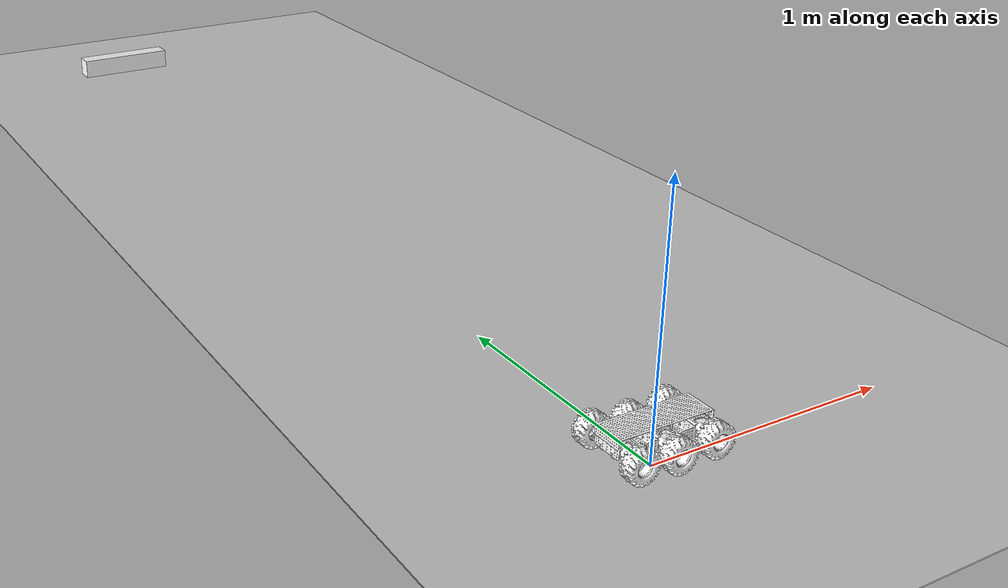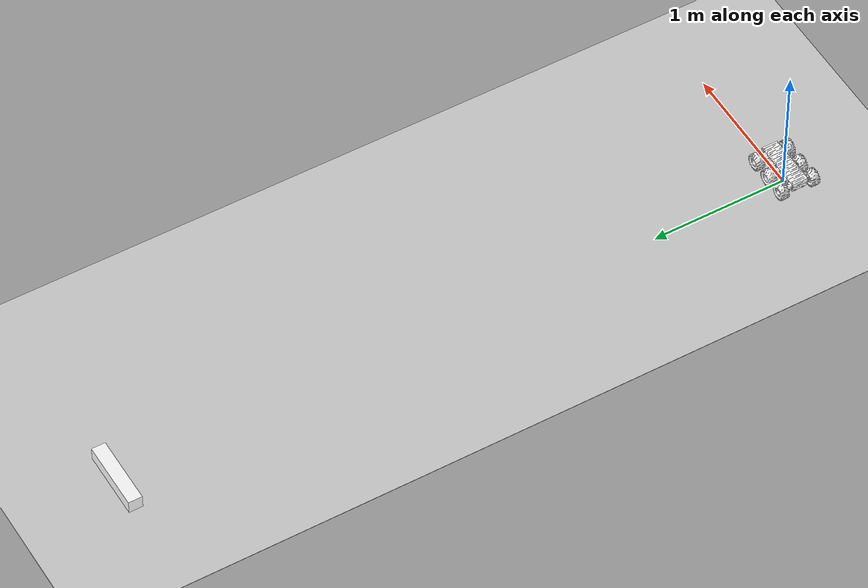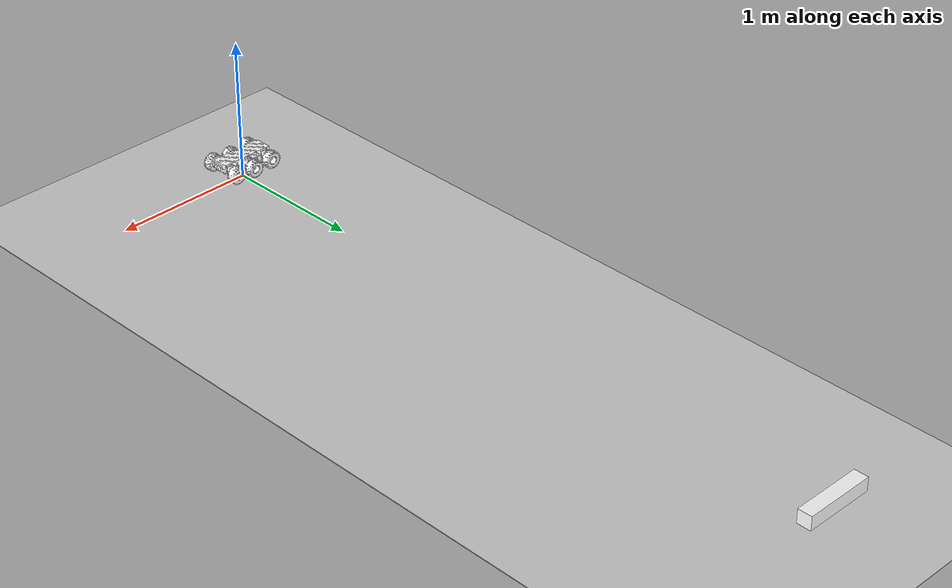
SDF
<sdf version="1.7">
 <world name="wildthumper_runway">
  <plugin filename="libignition-gazebo-physics-system.so" name="ignition::gazebo::systems::Physics"/>
  <plugin filename="libignition-gazebo-user-commands-system.so" name="ignition::gazebo::systems::UserCommands"/>
  <plugin filename="libignition-gazebo-scene-broadcaster-system.so" name="ignition::gazebo::systems::SceneBroadcaster"/>
  <plugin filename="libignition-gazebo-imu-system.so" name="ignition::gazebo::systems::Imu"/>
  <scene><ambient>1.0 1.0 1.0</ambient><background>0.8 0.8 0.8</background></scene>
  <light type="directional" name="sun">
   <pose>0 0 10 0 0 0</pose>
   <diffuse>0.8 0.8 0.8 1</diffuse>
   <specular>0.8 0.8 0.8 1</specular>
   <attenuation>
    <range>1000</range>
    <constant>0.9</constant>
    <linear>0.01</linear>
    <quadratic>0.001</quadratic>
   </attenuation>
   <direction>-0.5 0.1 -0.9</direction>
  </light>
  <include><uri>model://runway</uri></include>
  <model name="stand">
   <pose>0 5 0.05 0 0 0</pose>
   <static>1</static>
   <link name="base_link">
    <visual name="visual">
     <geometry><box><size>0.5 0.1 0.1</size></box></geometry>
     <material>
      <ambient>1 1 1</ambient>
      <diffuse>1 1 1</diffuse>
      <specular>1 1 1</specular>
      <pbr>
       <metal>
        <albedo_map>model://wildthumper/materials/textures/silver_metal/silver_metal_diffuse.jpg</albedo_map>
        <metalness_map>model://wildthumper/materials/textures/silver_metal/silver_metal_metallic.jpg</metalness_map>
        <normal_map>model://wildthumper/materials/textures/silver_metal/silver_metal_normal.jpg</normal_map>
        <roughness_map>model://wildthumper/materials/textures/silver_metal/silver_metal_roughness.jpg</roughness_map>
        <roughness>1.0</roughness>
        <metalness>1.0</metalness>
       </metal>
      </pbr>
     </material>
    </visual>
    <collision name="collision"><geometry><box><size>0.5 0.1 0.1</size></box></geometry></collision>
   </link>
  </model>
  <include><pose>0 0 0.15 0 0 0</pose><uri>model://wildthumper</uri></include>
 </world>
</sdf>

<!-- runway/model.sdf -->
<sdf version="1.9">
  <model name="runway">
    <static>true</static>
    <link name="link">
      <collision name="collision">
        <geometry>
          <plane>
            <normal>0 0 1</normal>
          </plane>
        </geometry>
      </collision>
      <visual name="runway">
        <pose degrees="true">0 0 0 0 0 90</pose>
        <cast_shadows>false</cast_shadows>
        <geometry>
          <plane>
            <normal>0 0 1</normal>
            <size>1500 100</size>
          </plane>
        </geometry>
        <material>
          <ambient>0.8 0.8 0.8 1</ambient>
          <diffuse>0.8 0.8 0.8 1</diffuse>
          <specular>0.1 0.1 0.1 1</specular>
          <pbr>
            <metal>
              <albedo_map>materials/textures/runway.png</albedo_map>
              <roughness>0.6</roughness>
              <metalness>0</metalness>
            </metal>
          </pbr>
        </material>
      </visual>
      <visual name="airfield">
        <pose>0 0 -0.01 0 0 0</pose>
        <cast_shadows>false</cast_shadows>
        <geometry>
          <mesh>
            <uri>model://runway/meshes/airfield.dae</uri>
          </mesh>
        </geometry>
        <material>
          <ambient>0.8 0.8 0.8 1</ambient>
          <diffuse>0.8 0.8 0.8 1</diffuse>
          <specular>0.1 0.1 0.1 1</specular>
          <pbr>
            <metal>
              <albedo_map>materials/textures/Grass004_2K_Color.jpg</albedo_map>
              <ambient_occlusion_map>materials/textures/Grass004_2K_AmbientOcclusion.jpg</ambient_occlusion_map>
              <normal_map>materials/textures/Grass004_2K_NormalGL.jpg</normal_map>
              <roughness_map>materials/textures/Grass004_2K_Roughness.jpg</roughness_map>
              <roughness>0.6</roughness>
              <metalness>0</metalness>
            </metal>
          </pbr>
        </material>
      </visual>
    </link>
  </model>
</sdf>

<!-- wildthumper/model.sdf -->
<sdf version='1.9'>
  <model name='wildthumper'>
    <static>0</static>
    <self_collide>0</self_collide>

    <link name='base_link'>
      <inertial>
        <pose>0 0 0 0 0 0</pose>
        <mass>0.01</mass>
        <inertia>
          <ixx>0.01</ixx>
          <ixy>0</ixy>
          <ixz>0</ixz>
          <iyy>0.01</iyy>
          <iyz>0</iyz>
          <izz>0.01</izz>
        </inertia>
      </inertial>
      <collision name='base_link_collision'>
        <pose>0 0 0 0 0 0</pose>
        <geometry>
          <box>
            <size>0.001 0.001 0.001</size>
          </box>
        </geometry>
      </collision>
      <visual name='base_link_visual'>
        <pose>0 0 0 0 0 0</pose>
        <geometry>
          <box>
            <size>0.001 0.001 0.001</size>
          </box>
        </geometry>
        <material>
          <script>
            <name>Gazebo/Orange</name>
            <uri>file://media/materials/scripts/gazebo.material</uri>
          </script>
          <diffuse>1 0.3125 0 1</diffuse>
          <ambient>1 0.3125 0 1</ambient>
        </material>
      </visual>
    </link>
    <joint name='front_small_chassis_joint' type='fixed'>
      <pose relative_to='base_link'>0.075 0 -0.02 0 0 0</pose>
      <parent>base_link</parent>
      <child>front_small_chassis_link</child>
      <axis>
        <dynamics>
          <damping>1.0</damping>
        </dynamics>
        <xyz>0 0 1</xyz>
        <limit>
          <lower>-1e16</lower>
          <upper>1e16</upper>
        </limit>
      </axis>
    </joint>
    <link name='front_small_chassis_link'>
      <pose relative_to='front_small_chassis_joint'>0 0 0 0 0 0</pose>
      <inertial>
        <pose>0 0 0 0 0 0</pose>
        <mass>0.2</mass>
        <inertia>
          <ixx>0.0002666666666666667</ixx>
          <ixy>0</ixy>
          <ixz>0</ixz>
          <iyy>0.0001083333333333333</iyy>
          <iyz>0</iyz>
          <izz>0.0003216666666666667</izz>
        </inertia>
      </inertial>
      <collision name='front_small_chassis_link_collision'>
        <pose>0 0 0 0 0 0</pose>
        <geometry>
          <box>
            <size>0.07000000000000001 0.12 0.04</size>
          </box>
        </geometry>
      </collision>
      <visual name='front_small_chassis_link_visual'>
        <pose>0 0 0 0 0 0</pose>
        <geometry>
          <mesh>
            <scale>1 1 1</scale>
            <uri>model://wildthumper/meshes/bases/small_chassis_with_frame_connector.dae</uri>
          </mesh>
        </geometry>
        <material>
          <ambient>1 1 1</ambient>
          <diffuse>1 1 1</diffuse>
          <specular>1 1 1</specular>
          <pbr>
            <metal>
              <albedo_map>model://wildthumper/materials/textures/black_metal/black_metal_diffuse.jpg</albedo_map>
              <metalness_map>model://wildthumper/materials/textures/black_metal/black_metal_metallic.jpg</metalness_map>
              <normal_map>model://wildthumper/materials/textures/black_metal/black_metal_normal.jpg</normal_map>
              <roughness_map>model://wildthumper/materials/textures/black_metal/black_metal_roughness.jpg</roughness_map>
              <roughness>1.0</roughness>
              <metalness>1.0</metalness>
            </metal>
          </pbr>
        </material>
      </visual>
    </link>
    <joint name='front_wheel_chassis_short_joint' type='fixed'>
      <pose relative_to='base_link'>0.15 0 -0.02 0 0 0</pose>
      <parent>base_link</parent>
      <child>front_wheel_chassis_short_link</child>
      <axis>
        <dynamics>
          <damping>1.0</damping>
        </dynamics>
        <xyz>0 0 1</xyz>
        <limit>
          <lower>-1e16</lower>
          <upper>1e16</upper>
        </limit>
      </axis>
    </joint>
    <link name='front_wheel_chassis_short_link'>
      <pose relative_to='front_wheel_chassis_short_joint'>0 0 0 0 0 0</pose>
      <inertial>
        <pose>0 0 0 0 0 0</pose>
        <mass>0.2</mass>
        <inertia>
          <ixx>0.0002666666666666667</ixx>
          <ixy>0</ixy>
          <ixz>0</ixz>
          <iyy>0.0001083333333333333</iyy>
          <iyz>0</iyz>
          <izz>0.0003216666666666667</izz>
        </inertia>
      </inertial>
      <collision name='front_wheel_chassis_short_link_collision'>
        <pose>0 0 0 0 0 0</pose>
        <geometry>
          <box>
            <size>0.07000000000000001 0.12 0.04</size>
          </box>
        </geometry>
      </collision>
      <visual name='front_wheel_chassis_short_link_visual'>
        <pose>0 0 0 0 0 0</pose>
        <geometry>
          <mesh>
            <scale>1 1 1</scale>
            <uri>model://wildthumper/meshes/bases/wheel_chassis_short.dae</uri>
          </mesh>
        </geometry>
        <material>
          <ambient>1 1 1</ambient>
          <diffuse>1 1 1</diffuse>
          <specular>1 1 1</specular>
          <pbr>
            <metal>
              <albedo_map>model://wildthumper/materials/textures/black_metal/black_metal_diffuse.jpg</albedo_map>
              <metalness_map>model://wildthumper/materials/textures/black_metal/black_metal_metallic.jpg</metalness_map>
              <normal_map>model://wildthumper/materials/textures/black_metal/black_metal_normal.jpg</normal_map>
              <roughness_map>model://wildthumper/materials/textures/black_metal/black_metal_roughness.jpg</roughness_map>
              <roughness>1.0</roughness>
              <metalness>1.0</metalness>
            </metal>
          </pbr>
        </material>
      </visual>
    </link>
    <joint name='front_left_motor_asm_joint' type='revolute'>
      <pose relative_to='front_wheel_chassis_short_link'>0 0.03 -0.01 0 0 0</pose>
      <parent>front_wheel_chassis_short_link</parent>
      <child>front_left_motor_asm_link</child>
      <axis>
        <xyz>1 0 0</xyz>
        <limit>
          <lower>-0.5</lower>
          <upper>0.5</upper>
          <effort>50</effort>
          <velocity>10</velocity>
        </limit>
        <dynamics>
          <damping>0.7</damping>
          <friction>0</friction>
          <spring_reference>0</spring_reference>
          <spring_stiffness>3</spring_stiffness>
        </dynamics>
      </axis>
      <physics>
        <provide_feedback>true</provide_feedback>
        <ode>
          <implicit_spring_damper>true</implicit_spring_damper>
          <cfm_damping>true</cfm_damping>
          <limit>
            <cfm>0.0</cfm>
            <erp>0.2</erp>
          </limit>
          <provide_feedback>true</provide_feedback>
        </ode>
      </physics>
    </joint>
    <link name='front_left_motor_asm_link'>
      <pose relative_to='front_left_motor_asm_joint'>0 0 0 0 0 0</pose>
      <inertial>
        <pose>0 0.025 0 1.570796326794896 0 0</pose>
        <mass>0.1</mass>
        <inertia>
          <ixx>2.723333333333334e-05</ixx>
          <ixy>0</ixy>
          <ixz>0</ixz>
          <iyy>2.723333333333334e-05</iyy>
          <iyz>0</iyz>
          <izz>1.28e-05</izz>
        </inertia>
      </inertial>
      <collision name='front_left_motor_asm_link_collision'>
        <pose>0 0 0 0 1.570796326794897 0</pose>
        <geometry>
          <cylinder>
            <length>0.064</length>
            <radius>0.016</radius>
          </cylinder>
        </geometry>
      </collision>
      <collision name='front_left_motor_asm_link_collision_1'>
        <pose>0 0.025 0 1.570796326794896 0 0</pose>
        <geometry>
          <cylinder>
            <length>0.05</length>
            <radius>0.016</radius>
          </cylinder>
        </geometry>
      </collision>
      <visual name='front_left_motor_asm_link_visual'>
        <pose>0 0 0 0 0 0</pose>
        <geometry>
          <mesh>
            <scale>1 1 1</scale>
            <uri>model://wildthumper/meshes/bases/left_motor_asm.dae</uri>
          </mesh>
        </geometry>
        <material>
          <ambient>1 1 1</ambient>
          <diffuse>1 1 1</diffuse>
          <specular>1 1 1</specular>
          <pbr>
            <metal>
              <albedo_map>model://wildthumper/materials/textures/black_metal/black_metal_diffuse.jpg</albedo_map>
              <metalness_map>model://wildthumper/materials/textures/black_metal/black_metal_metallic.jpg</metalness_map>
              <normal_map>model://wildthumper/materials/textures/black_metal/black_metal_normal.jpg</normal_map>
              <roughness_map>model://wildthumper/materials/textures/black_metal/black_metal_roughness.jpg</roughness_map>
              <roughness>1.0</roughness>
              <metalness>1.0</metalness>
            </metal>
          </pbr>
        </material>
      </visual>
    </link>
    <joint name='front_left_wheel_joint' type='revolute'>
      <pose relative_to='front_left_motor_asm_link'>0 0.09 0 0 0 0</pose>
      <parent>front_left_motor_asm_link</parent>
      <child>front_left_wheel_link</child>
      <axis>
        <xyz>0 1 0</xyz>
        <limit>
          <lower>-1e16</lower>
          <upper>1e16</upper>
        </limit>
        <dynamics>
          <damping>0.02</damping>
        </dynamics>
      </axis>
    </joint>
    <link name='front_left_wheel_link'>
      <pose relative_to='front_left_wheel_joint'>0 0 0 0 0 0</pose>
      <inertial>
        <pose>0 0 0 1.570796326794896 0 0</pose>
        <mass>0.19</mass>
        <inertia>
          <ixx>0.0002022409166666667</ixx>
          <ixy>0</ixy>
          <ixz>0</ixz>
          <iyy>0.0002022409166666667</iyy>
          <iyz>1.203706215242022e-35</iyz>
          <izz>0.0002973904999999999</izz>
        </inertia>
      </inertial>
      <collision name='front_left_wheel_link_collision'>
        <pose>0 0 0 1.570796326794896 0 0</pose>
        <geometry>
          <cylinder>
            <length>0.062</length>
            <radius>0.062</radius>
          </cylinder>
        </geometry>
        <surface>
          <friction>
            <ode>
              <mu>10.0</mu>
              <mu2>5.0</mu2>
              <fdir1>1 0 0</fdir1>
              <slip1>0.0</slip1>
              <slip2>0.0</slip2>
            </ode>
          </friction>
        </surface>
      </collision>
      <collision name='front_left_wheel_link_fixed_joint_lump__front_left_wheel_adapter_link_collision_1'>
        <pose>0 0 0 1.570796326794896 0 0</pose>
        <geometry>
          <cylinder>
            <length>0.024</length>
            <radius>0.005</radius>
          </cylinder>
        </geometry>
      </collision>
      <collision name='front_left_wheel_link_fixed_joint_lump__front_left_wheel_rim_link_collision_2'>
        <pose>0 0 0 1.570796326794896 0 0</pose>
        <geometry>
          <cylinder>
            <length>0.05</length>
            <radius>0.03</radius>
          </cylinder>
        </geometry>
      </collision>
      <visual name='front_left_wheel_link_visual'>
        <pose>0 0 0 0 0 0</pose>
        <geometry>
          <mesh>
            <scale>1 1 1</scale>
            <uri>model://wildthumper/meshes/wheels/left_wheel_tyre.dae</uri>
          </mesh>
        </geometry>
        <material>
          <ambient>1 1 1</ambient>
          <diffuse>1 1 1</diffuse>
          <specular>1 1 1</specular>
          <pbr>
            <metal>
              <albedo_map>model://wildthumper/materials/textures/rubber_01/rubber_01_diffuse.jpg</albedo_map>
              <normal_map>model://wildthumper/materials/textures/rubber_01/rubber_01_normal.jpg</normal_map>
              <roughness_map>model://wildthumper/materials/textures/rubber_01/rubber_01_roughness.jpg</roughness_map>
              <roughness>1.0</roughness>
              <metalness>0.0</metalness>
            </metal>
          </pbr>
        </material>
      </visual>
      <visual name='front_left_wheel_link_fixed_joint_lump__front_left_wheel_adapter_link_visual_1'>
        <pose>0 0 0 0 0 0</pose>
        <geometry>
          <mesh>
            <scale>1 1 1</scale>
            <uri>model://wildthumper/meshes/wheels/left_wheel_adapter.dae</uri>
          </mesh>
        </geometry>
        <material>
          <ambient>1 1 1</ambient>
          <diffuse>1 1 1</diffuse>
          <specular>1 1 1</specular>
          <pbr>
            <metal>
              <albedo_map>model://wildthumper/materials/textures/silver_metal/silver_metal_diffuse.jpg</albedo_map>
              <metalness_map>model://wildthumper/materials/textures/silver_metal/silver_metal_metallic.jpg</metalness_map>
              <normal_map>model://wildthumper/materials/textures/silver_metal/silver_metal_normal.jpg</normal_map>
              <roughness_map>model://wildthumper/materials/textures/silver_metal/silver_metal_roughness.jpg</roughness_map>
              <roughness>1.0</roughness>
              <metalness>1.0</metalness>
            </metal>
          </pbr>
        </material>
      </visual>
      <visual name='front_left_wheel_link_fixed_joint_lump__front_left_wheel_rim_link_visual_2'>
        <pose>0 0 0 0 0 0</pose>
        <geometry>
          <mesh>
            <scale>1 1 1</scale>
            <uri>model://wildthumper/meshes/wheels/left_wheel_rim.dae</uri>
          </mesh>
        </geometry>
        <material>
          <ambient>1 1 1</ambient>
          <diffuse>1 1 1</diffuse>
          <specular>1 1 1</specular>
          <pbr>
            <metal>
              <albedo_map>model://wildthumper/materials/textures/red_metal/red_metal_diffuse.jpg</albedo_map>
              <metalness_map>model://wildthumper/materials/textures/red_metal/red_metal_metallic.jpg</metalness_map>
              <normal_map>model://wildthumper/materials/textures/red_metal/red_metal_normal.jpg</normal_map>
              <roughness_map>model://wildthumper/materials/textures/red_metal/red_metal_roughness.jpg</roughness_map>
              <roughness>1.0</roughness>
              <metalness>1.0</metalness>
            </metal>
          </pbr>
        </material>
      </visual>
    </link>
    <joint name='front_right_motor_asm_joint' type='revolute'>
      <pose relative_to='front_wheel_chassis_short_link'>0 -0.03 -0.01 0 0 0</pose>
      <parent>front_wheel_chassis_short_link</parent>
      <child>front_right_motor_asm_link</child>
      <axis>
        <xyz>1 0 0</xyz>
        <limit>
          <lower>-0.5</lower>
          <upper>0.5</upper>
          <effort>50</effort>
          <velocity>10</velocity>
        </limit>
        <dynamics>
          <damping>0.7</damping>
          <friction>0</friction>
          <spring_reference>0</spring_reference>
          <spring_stiffness>3</spring_stiffness>
        </dynamics>
      </axis>
    </joint>
    <link name='front_right_motor_asm_link'>
      <pose relative_to='front_right_motor_asm_joint'>0 0 0 0 0 0</pose>
      <inertial>
        <pose>0 -0.025 0 1.570796326794896 0 0</pose>
        <mass>0.1</mass>
        <inertia>
          <ixx>2.723333333333334e-05</ixx>
          <ixy>0</ixy>
          <ixz>0</ixz>
          <iyy>2.723333333333334e-05</iyy>
          <iyz>0</iyz>
          <izz>1.28e-05</izz>
        </inertia>
      </inertial>
      <collision name='front_right_motor_asm_link_collision'>
        <pose>0 0 0 0 1.570796326794897 0</pose>
        <geometry>
          <cylinder>
            <length>0.064</length>
            <radius>0.016</radius>
          </cylinder>
        </geometry>
      </collision>
      <collision name='front_right_motor_asm_link_collision_1'>
        <pose>0 -0.025 0 1.570796326794896 0 0</pose>
        <geometry>
          <cylinder>
            <length>0.05</length>
            <radius>0.016</radius>
          </cylinder>
        </geometry>
      </collision>
      <visual name='front_right_motor_asm_link_visual'>
        <pose>0 0 0 0 0 0</pose>
        <geometry>
          <mesh>
            <scale>1 1 1</scale>
            <uri>model://wildthumper/meshes/bases/right_motor_asm.dae</uri>
          </mesh>
        </geometry>
        <material>
          <ambient>1 1 1</ambient>
          <diffuse>1 1 1</diffuse>
          <specular>1 1 1</specular>
          <pbr>
            <metal>
              <albedo_map>model://wildthumper/materials/textures/black_metal/black_metal_diffuse.jpg</albedo_map>
              <metalness_map>model://wildthumper/materials/textures/black_metal/black_metal_metallic.jpg</metalness_map>
              <normal_map>model://wildthumper/materials/textures/black_metal/black_metal_normal.jpg</normal_map>
              <roughness_map>model://wildthumper/materials/textures/black_metal/black_metal_roughness.jpg</roughness_map>
              <roughness>1.0</roughness>
              <metalness>1.0</metalness>
            </metal>
          </pbr>
        </material>
      </visual>
    </link>
    <joint name='front_right_wheel_joint' type='revolute'>
      <pose relative_to='front_right_motor_asm_link'>0 -0.09 0 0 0 0</pose>
      <parent>front_right_motor_asm_link</parent>
      <child>front_right_wheel_link</child>
      <axis>
        <xyz>0 1 0</xyz>
        <limit>
          <lower>-1e16</lower>
          <upper>1e16</upper>
        </limit>
        <dynamics>
          <damping>0.02</damping>
        </dynamics>
      </axis>
    </joint>
    <link name='front_right_wheel_link'>
      <pose relative_to='front_right_wheel_joint'>0 0 0 0 0 0</pose>
      <inertial>
        <pose>0 0 0 1.570796326794896 0 0</pose>
        <mass>0.19</mass>
        <inertia>
          <ixx>0.0002022409166666667</ixx>
          <ixy>0</ixy>
          <ixz>0</ixz>
          <iyy>0.0002022409166666667</iyy>
          <iyz>1.203706215242022e-35</iyz>
          <izz>0.0002973904999999999</izz>
        </inertia>
      </inertial>
      <collision name='front_right_wheel_link_collision'>
        <pose>0 0 0 1.570796326794896 0 0</pose>
        <geometry>
          <cylinder>
            <length>0.062</length>
            <radius>0.062</radius>
          </cylinder>
        </geometry>
        <surface>
          <friction>
            <ode>
              <mu>10.0</mu>
              <mu2>5.0</mu2>
              <fdir1>1 0 0</fdir1>
              <slip1>0.0</slip1>
              <slip2>0.0</slip2>
            </ode>
          </friction>
        </surface>
      </collision>
      <collision name='front_right_wheel_link_fixed_joint_lump__front_right_wheel_adapter_link_collision_1'>
        <pose>0 0 0 1.570796326794896 0 0</pose>
        <geometry>
          <cylinder>
            <length>0.024</length>
            <radius>0.005</radius>
          </cylinder>
        </geometry>
      </collision>
      <collision name='front_right_wheel_link_fixed_joint_lump__front_right_wheel_rim_link_collision_2'>
        <pose>0 0 0 1.570796326794896 0 0</pose>
        <geometry>
          <cylinder>
            <length>0.05</length>
            <radius>0.03</radius>
          </cylinder>
        </geometry>
      </collision>
      <visual name='front_right_wheel_link_visual'>
        <pose>0 0 0 0 0 0</pose>
        <geometry>
          <mesh>
            <scale>1 1 1</scale>
            <uri>model://wildthumper/meshes/wheels/right_wheel_tyre.dae</uri>
          </mesh>
        </geometry>
        <material>
          <ambient>1 1 1</ambient>
          <diffuse>1 1 1</diffuse>
          <specular>1 1 1</specular>
          <pbr>
            <metal>
              <albedo_map>model://wildthumper/materials/textures/rubber_01/rubber_01_diffuse.jpg</albedo_map>
              <normal_map>model://wildthumper/materials/textures/rubber_01/rubber_01_normal.jpg</normal_map>
              <roughness_map>model://wildthumper/materials/textures/rubber_01/rubber_01_roughness.jpg</roughness_map>
              <roughness>1.0</roughness>
              <metalness>0.0</metalness>
            </metal>
          </pbr>
        </material>
      </visual>
      <visual name='front_right_wheel_link_fixed_joint_lump__front_right_wheel_adapter_link_visual_1'>
        <pose>0 0 0 0 0 0</pose>
        <geometry>
          <mesh>
            <scale>1 1 1</scale>
            <uri>model://wildthumper/meshes/wheels/right_wheel_adapter.dae</uri>
          </mesh>
        </geometry>
        <material>
          <ambient>1 1 1</ambient>
          <diffuse>1 1 1</diffuse>
          <specular>1 1 1</specular>
          <pbr>
            <metal>
              <albedo_map>model://wildthumper/materials/textures/silver_metal/silver_metal_diffuse.jpg</albedo_map>
              <metalness_map>model://wildthumper/materials/textures/silver_metal/silver_metal_metallic.jpg</metalness_map>
              <normal_map>model://wildthumper/materials/textures/silver_metal/silver_metal_normal.jpg</normal_map>
              <roughness_map>model://wildthumper/materials/textures/silver_metal/silver_metal_roughness.jpg</roughness_map>
              <roughness>1.0</roughness>
              <metalness>1.0</metalness>
            </metal>
          </pbr>
        </material>
      </visual>
      <visual name='front_right_wheel_link_fixed_joint_lump__front_right_wheel_rim_link_visual_2'>
        <pose>0 0 0 0 0 0</pose>
        <geometry>
          <mesh>
            <scale>1 1 1</scale>
            <uri>model://wildthumper/meshes/wheels/right_wheel_rim.dae</uri>
          </mesh>
        </geometry>
        <material>
          <ambient>1 1 1</ambient>
          <diffuse>1 1 1</diffuse>
          <specular>1 1 1</specular>
          <pbr>
            <metal>
              <albedo_map>model://wildthumper/materials/textures/red_metal/red_metal_diffuse.jpg</albedo_map>
              <metalness_map>model://wildthumper/materials/textures/red_metal/red_metal_metallic.jpg</metalness_map>
              <normal_map>model://wildthumper/materials/textures/red_metal/red_metal_normal.jpg</normal_map>
              <roughness_map>model://wildthumper/materials/textures/red_metal/red_metal_roughness.jpg</roughness_map>
              <roughness>1.0</roughness>
              <metalness>1.0</metalness>
            </metal>
          </pbr>
        </material>
      </visual>
    </link>
    <joint name='mid_wheel_chassis_long_joint' type='fixed'>
      <pose relative_to='base_link'>0 0 -0.025 0 0 0</pose>
      <parent>base_link</parent>
      <child>mid_wheel_chassis_long_link</child>
      <axis>
        <dynamics>
          <damping>1.0</damping>
        </dynamics>
        <xyz>0 0 1</xyz>
        <limit>
          <lower>-1e16</lower>
          <upper>1e16</upper>
        </limit>
      </axis>
    </joint>
    <link name='mid_wheel_chassis_long_link'>
      <pose relative_to='mid_wheel_chassis_long_joint'>0 0 0 0 0 0</pose>
      <inertial>
        <pose>0 0 0 0 0 0</pose>
        <mass>0.2</mass>
        <inertia>
          <ixx>0.0002816666666666667</ixx>
          <ixy>0</ixy>
          <ixz>0</ixz>
          <iyy>0.0001233333333333334</iyy>
          <iyz>0</iyz>
          <izz>0.0003216666666666667</izz>
        </inertia>
      </inertial>
      <collision name='mid_wheel_chassis_long_link_collision'>
        <pose>0 0 0 0 0 0</pose>
        <geometry>
          <box>
            <size>0.07000000000000001 0.12 0.05</size>
          </box>
        </geometry>
      </collision>
      <visual name='mid_wheel_chassis_long_link_visual'>
        <pose>0 0 0.005 0 0 0</pose>
        <geometry>
          <mesh>
            <scale>1 1 1</scale>
            <uri>model://wildthumper/meshes/bases/wheel_chassis_long.dae</uri>
          </mesh>
        </geometry>
        <material>
          <ambient>1 1 1</ambient>
          <diffuse>1 1 1</diffuse>
          <specular>1 1 1</specular>
          <pbr>
            <metal>
              <albedo_map>model://wildthumper/materials/textures/black_metal/black_metal_diffuse.jpg</albedo_map>
              <metalness_map>model://wildthumper/materials/textures/black_metal/black_metal_metallic.jpg</metalness_map>
              <normal_map>model://wildthumper/materials/textures/black_metal/black_metal_normal.jpg</normal_map>
              <roughness_map>model://wildthumper/materials/textures/black_metal/black_metal_roughness.jpg</roughness_map>
              <roughness>1.0</roughness>
              <metalness>1.0</metalness>
            </metal>
          </pbr>
        </material>
      </visual>
    </link>
    <joint name='mid_left_motor_asm_joint' type='revolute'>
      <pose relative_to='mid_wheel_chassis_long_link'>0 0.03 -0.015 0 0 0</pose>
      <parent>mid_wheel_chassis_long_link</parent>
      <child>mid_left_motor_asm_link</child>
      <axis>
        <xyz>1 0 0</xyz>
        <limit>
          <lower>-0.5</lower>
          <upper>0.5</upper>
          <effort>50</effort>
          <velocity>10</velocity>
        </limit>
        <dynamics>
          <damping>0.7</damping>
          <friction>0</friction>
          <spring_reference>0</spring_reference>
          <spring_stiffness>3</spring_stiffness>
        </dynamics>
      </axis>
    </joint>
    <link name='mid_left_motor_asm_link'>
      <pose relative_to='mid_left_motor_asm_joint'>0 0 0 0 0 0</pose>
      <inertial>
        <pose>0 0.025 0 1.570796326794896 0 0</pose>
        <mass>0.1</mass>
        <inertia>
          <ixx>2.723333333333334e-05</ixx>
          <ixy>0</ixy>
          <ixz>0</ixz>
          <iyy>2.723333333333334e-05</iyy>
          <iyz>0</iyz>
          <izz>1.28e-05</izz>
        </inertia>
      </inertial>
      <collision name='mid_left_motor_asm_link_collision'>
        <pose>0 0 0 0 1.570796326794897 0</pose>
        <geometry>
          <cylinder>
            <length>0.064</length>
            <radius>0.016</radius>
          </cylinder>
        </geometry>
      </collision>
      <collision name='mid_left_motor_asm_link_collision_1'>
        <pose>0 0.025 0 1.570796326794896 0 0</pose>
        <geometry>
          <cylinder>
            <length>0.05</length>
            <radius>0.016</radius>
          </cylinder>
        </geometry>
      </collision>
      <visual name='mid_left_motor_asm_link_visual'>
        <pose>0 0 0 0 0 0</pose>
        <geometry>
          <mesh>
            <scale>1 1 1</scale>
            <uri>model://wildthumper/meshes/bases/left_motor_asm.dae</uri>
          </mesh>
        </geometry>
        <material>
          <ambient>1 1 1</ambient>
          <diffuse>1 1 1</diffuse>
          <specular>1 1 1</specular>
          <pbr>
            <metal>
              <albedo_map>model://wildthumper/materials/textures/black_metal/black_metal_diffuse.jpg</albedo_map>
              <metalness_map>model://wildthumper/materials/textures/black_metal/black_metal_metallic.jpg</metalness_map>
              <normal_map>model://wildthumper/materials/textures/black_metal/black_metal_normal.jpg</normal_map>
              <roughness_map>model://wildthumper/materials/textures/black_metal/black_metal_roughness.jpg</roughness_map>
              <roughness>1.0</roughness>
              <metalness>1.0</metalness>
            </metal>
          </pbr>
        </material>
      </visual>
    </link>
    <joint name='mid_left_wheel_joint' type='revolute'>
      <pose relative_to='mid_left_motor_asm_link'>0 0.09 0 0 0 0</pose>
      <parent>mid_left_motor_asm_link</parent>
      <child>mid_left_wheel_link</child>
      <axis>
        <xyz>0 1 0</xyz>
        <limit>
          <lower>-1e16</lower>
          <upper>1e16</upper>
        </limit>
        <dynamics>
          <damping>0.02</damping>
        </dynamics>
      </axis>
    </joint>
    <link name='mid_left_wheel_link'>
      <pose relative_to='mid_left_wheel_joint'>0 0 0 0 0 0</pose>
      <inertial>
        <pose>0 0 0 1.570796326794896 0 0</pose>
        <mass>0.19</mass>
        <inertia>
          <ixx>0.0002022409166666667</ixx>
          <ixy>0</ixy>
          <ixz>0</ixz>
          <iyy>0.0002022409166666667</iyy>
          <iyz>1.203706215242022e-35</iyz>
          <izz>0.0002973904999999999</izz>
        </inertia>
      </inertial>
      <collision name='mid_left_wheel_link_collision'>
        <pose>0 0 0 1.570796326794896 0 0</pose>
        <geometry>
          <cylinder>
            <length>0.062</length>
            <radius>0.062</radius>
          </cylinder>
        </geometry>
        <surface>
          <friction>
            <ode>
              <mu>10.0</mu>
              <mu2>5.0</mu2>
              <fdir1>1 0 0</fdir1>
              <slip1>0.0</slip1>
              <slip2>0.0</slip2>
            </ode>
          </friction>
        </surface>
      </collision>
      <collision name='mid_left_wheel_link_fixed_joint_lump__mid_left_wheel_adapter_link_collision_1'>
        <pose>0 0 0 1.570796326794896 0 0</pose>
        <geometry>
          <cylinder>
            <length>0.024</length>
            <radius>0.005</radius>
          </cylinder>
        </geometry>
      </collision>
      <collision name='mid_left_wheel_link_fixed_joint_lump__mid_left_wheel_rim_link_collision_2'>
        <pose>0 0 0 1.570796326794896 0 0</pose>
        <geometry>
          <cylinder>
            <length>0.05</length>
            <radius>0.03</radius>
          </cylinder>
        </geometry>
      </collision>
      <visual name='mid_left_wheel_link_visual'>
        <pose>0 0 0 0 0 0</pose>
        <geometry>
          <mesh>
            <scale>1 1 1</scale>
            <uri>model://wildthumper/meshes/wheels/left_wheel_tyre.dae</uri>
          </mesh>
        </geometry>
        <material>
          <ambient>1 1 1</ambient>
          <diffuse>1 1 1</diffuse>
          <specular>1 1 1</specular>
          <pbr>
            <metal>
              <albedo_map>model://wildthumper/materials/textures/rubber_01/rubber_01_diffuse.jpg</albedo_map>
              <normal_map>model://wildthumper/materials/textures/rubber_01/rubber_01_normal.jpg</normal_map>
              <roughness_map>model://wildthumper/materials/textures/rubber_01/rubber_01_roughness.jpg</roughness_map>
              <roughness>1.0</roughness>
              <metalness>0.0</metalness>
            </metal>
          </pbr>
        </material>
      </visual>
      <visual name='mid_left_wheel_link_fixed_joint_lump__mid_left_wheel_adapter_link_visual_1'>
        <pose>0 0 0 0 0 0</pose>
        <geometry>
          <mesh>
            <scale>1 1 1</scale>
            <uri>model://wildthumper/meshes/wheels/left_wheel_adapter.dae</uri>
          </mesh>
        </geometry>
        <material>
          <ambient>1 1 1</ambient>
          <diffuse>1 1 1</diffuse>
          <specular>1 1 1</specular>
          <pbr>
            <metal>
              <albedo_map>model://wildthumper/materials/textures/silver_metal/silver_metal_diffuse.jpg</albedo_map>
              <metalness_map>model://wildthumper/materials/textures/silver_metal/silver_metal_metallic.jpg</metalness_map>
              <normal_map>model://wildthumper/materials/textures/silver_metal/silver_metal_normal.jpg</normal_map>
              <roughness_map>model://wildthumper/materials/textures/silver_metal/silver_metal_roughness.jpg</roughness_map>
              <roughness>1.0</roughness>
              <metalness>1.0</metalness>
            </metal>
          </pbr>
        </material>
      </visual>
      <visual name='mid_left_wheel_link_fixed_joint_lump__mid_left_wheel_rim_link_visual_2'>
        <pose>0 0 0 0 0 0</pose>
        <geometry>
          <mesh>
            <scale>1 1 1</scale>
            <uri>model://wildthumper/meshes/wheels/left_wheel_rim.dae</uri>
          </mesh>
        </geometry>
        <material>
          <ambient>1 1 1</ambient>
          <diffuse>1 1 1</diffuse>
          <specular>1 1 1</specular>
          <pbr>
            <metal>
              <albedo_map>model://wildthumper/materials/textures/red_metal/red_metal_diffuse.jpg</albedo_map>
              <metalness_map>model://wildthumper/materials/textures/red_metal/red_metal_metallic.jpg</metalness_map>
              <normal_map>model://wildthumper/materials/textures/red_metal/red_metal_normal.jpg</normal_map>
              <roughness_map>model://wildthumper/materials/textures/red_metal/red_metal_roughness.jpg</roughness_map>
              <roughness>1.0</roughness>
              <metalness>1.0</metalness>
            </metal>
          </pbr>
        </material>
      </visual>
    </link>
    <joint name='mid_right_motor_asm_joint' type='revolute'>
      <pose relative_to='mid_wheel_chassis_long_link'>0 -0.03 -0.015 0 0 0</pose>
      <parent>mid_wheel_chassis_long_link</parent>
      <child>mid_right_motor_asm_link</child>
      <axis>
        <xyz>1 0 0</xyz>
        <limit>
          <lower>-0.5</lower>
          <upper>0.5</upper>
          <effort>50</effort>
          <velocity>10</velocity>
        </limit>
        <dynamics>
          <damping>0.7</damping>
          <friction>0</friction>
          <spring_reference>0</spring_reference>
          <spring_stiffness>3</spring_stiffness>
        </dynamics>
      </axis>
    </joint>
    <link name='mid_right_motor_asm_link'>
      <pose relative_to='mid_right_motor_asm_joint'>0 0 0 0 0 0</pose>
      <inertial>
        <pose>0 -0.025 0 1.570796326794896 0 0</pose>
        <mass>0.1</mass>
        <inertia>
          <ixx>2.723333333333334e-05</ixx>
          <ixy>0</ixy>
          <ixz>0</ixz>
          <iyy>2.723333333333334e-05</iyy>
          <iyz>0</iyz>
          <izz>1.28e-05</izz>
        </inertia>
      </inertial>
      <collision name='mid_right_motor_asm_link_collision'>
        <pose>0 0 0 0 1.570796326794897 0</pose>
        <geometry>
          <cylinder>
            <length>0.064</length>
            <radius>0.016</radius>
          </cylinder>
        </geometry>
      </collision>
      <collision name='mid_right_motor_asm_link_collision_1'>
        <pose>0 -0.025 0 1.570796326794896 0 0</pose>
        <geometry>
          <cylinder>
            <length>0.05</length>
            <radius>0.016</radius>
          </cylinder>
        </geometry>
      </collision>
      <visual name='mid_right_motor_asm_link_visual'>
        <pose>0 0 0 0 0 0</pose>
        <geometry>
          <mesh>
            <scale>1 1 1</scale>
            <uri>model://wildthumper/meshes/bases/right_motor_asm.dae</uri>
          </mesh>
        </geometry>
        <material>
          <ambient>1 1 1</ambient>
          <diffuse>1 1 1</diffuse>
          <specular>1 1 1</specular>
          <pbr>
            <metal>
              <albedo_map>model://wildthumper/materials/textures/black_metal/black_metal_diffuse.jpg</albedo_map>
              <metalness_map>model://wildthumper/materials/textures/black_metal/black_metal_metallic.jpg</metalness_map>
              <normal_map>model://wildthumper/materials/textures/black_metal/black_metal_normal.jpg</normal_map>
              <roughness_map>model://wildthumper/materials/textures/black_metal/black_metal_roughness.jpg</roughness_map>
              <roughness>1.0</roughness>
              <metalness>1.0</metalness>
            </metal>
          </pbr>
        </material>
      </visual>
    </link>
    <joint name='mid_right_wheel_joint' type='revolute'>
      <pose relative_to='mid_right_motor_asm_link'>0 -0.09 0 0 0 0</pose>
      <parent>mid_right_motor_asm_link</parent>
      <child>mid_right_wheel_link</child>
      <axis>
        <xyz>0 1 0</xyz>
        <limit>
          <lower>-1e16</lower>
          <upper>1e16</upper>
        </limit>
        <dynamics>
          <damping>0.02</damping>
        </dynamics>
      </axis>
    </joint>
    <link name='mid_right_wheel_link'>
      <pose relative_to='mid_right_wheel_joint'>0 0 0 0 0 0</pose>
      <inertial>
        <pose>0 0 0 1.570796326794896 0 0</pose>
        <mass>0.19</mass>
        <inertia>
          <ixx>0.0002022409166666667</ixx>
          <ixy>0</ixy>
          <ixz>0</ixz>
          <iyy>0.0002022409166666667</iyy>
          <iyz>1.203706215242022e-35</iyz>
          <izz>0.0002973904999999999</izz>
        </inertia>
      </inertial>
      <collision name='mid_right_wheel_link_collision'>
        <pose>0 0 0 1.570796326794896 0 0</pose>
        <geometry>
          <cylinder>
            <length>0.062</length>
            <radius>0.062</radius>
          </cylinder>
        </geometry>
        <surface>
          <friction>
            <ode>
              <mu>10.0</mu>
              <mu2>5.0</mu2>
              <fdir1>1 0 0</fdir1>
              <slip1>0.0</slip1>
              <slip2>0.0</slip2>
            </ode>
          </friction>
        </surface>
      </collision>
      <collision name='mid_right_wheel_link_fixed_joint_lump__mid_right_wheel_adapter_link_collision_1'>
        <pose>0 0 0 1.570796326794896 0 0</pose>
        <geometry>
          <cylinder>
            <length>0.024</length>
            <radius>0.005</radius>
          </cylinder>
        </geometry>
      </collision>
      <collision name='mid_right_wheel_link_fixed_joint_lump__mid_right_wheel_rim_link_collision_2'>
        <pose>0 0 0 1.570796326794896 0 0</pose>
        <geometry>
          <cylinder>
            <length>0.05</length>
            <radius>0.03</radius>
          </cylinder>
        </geometry>
      </collision>
      <visual name='mid_right_wheel_link_visual'>
        <pose>0 0 0 0 0 0</pose>
        <geometry>
          <mesh>
            <scale>1 1 1</scale>
            <uri>model://wildthumper/meshes/wheels/right_wheel_tyre.dae</uri>
          </mesh>
        </geometry>
        <material>
          <ambient>1 1 1</ambient>
          <diffuse>1 1 1</diffuse>
          <specular>1 1 1</specular>
          <pbr>
            <metal>
              <albedo_map>model://wildthumper/materials/textures/rubber_01/rubber_01_diffuse.jpg</albedo_map>
              <normal_map>model://wildthumper/materials/textures/rubber_01/rubber_01_normal.jpg</normal_map>
              <roughness_map>model://wildthumper/materials/textures/rubber_01/rubber_01_roughness.jpg</roughness_map>
              <roughness>1.0</roughness>
              <metalness>0.0</metalness>
            </metal>
          </pbr>
        </material>
      </visual>
      <visual name='mid_right_wheel_link_fixed_joint_lump__mid_right_wheel_adapter_link_visual_1'>
        <pose>0 0 0 0 0 0</pose>
        <geometry>
          <mesh>
            <scale>1 1 1</scale>
            <uri>model://wildthumper/meshes/wheels/right_wheel_adapter.dae</uri>
          </mesh>
        </geometry>
        <material>
          <ambient>1 1 1</ambient>
          <diffuse>1 1 1</diffuse>
          <specular>1 1 1</specular>
          <pbr>
            <metal>
              <albedo_map>model://wildthumper/materials/textures/silver_metal/silver_metal_diffuse.jpg</albedo_map>
              <metalness_map>model://wildthumper/materials/textures/silver_metal/silver_metal_metallic.jpg</metalness_map>
              <normal_map>model://wildthumper/materials/textures/silver_metal/silver_metal_normal.jpg</normal_map>
              <roughness_map>model://wildthumper/materials/textures/silver_metal/silver_metal_roughness.jpg</roughness_map>
              <roughness>1.0</roughness>
              <metalness>1.0</metalness>
            </metal>
          </pbr>
        </material>
      </visual>
      <visual name='mid_right_wheel_link_fixed_joint_lump__mid_right_wheel_rim_link_visual_2'>
        <pose>0 0 0 0 0 0</pose>
        <geometry>
          <mesh>
            <scale>1 1 1</scale>
            <uri>model://wildthumper/meshes/wheels/right_wheel_rim.dae</uri>
          </mesh>
        </geometry>
        <material>
          <ambient>1 1 1</ambient>
          <diffuse>1 1 1</diffuse>
          <specular>1 1 1</specular>
          <pbr>
            <metal>
              <albedo_map>model://wildthumper/materials/textures/red_metal/red_metal_diffuse.jpg</albedo_map>
              <metalness_map>model://wildthumper/materials/textures/red_metal/red_metal_metallic.jpg</metalness_map>
              <normal_map>model://wildthumper/materials/textures/red_metal/red_metal_normal.jpg</normal_map>
              <roughness_map>model://wildthumper/materials/textures/red_metal/red_metal_roughness.jpg</roughness_map>
              <roughness>1.0</roughness>
              <metalness>1.0</metalness>
            </metal>
          </pbr>
        </material>
      </visual>
    </link>
    <joint name='rear_small_chassis_joint' type='fixed'>
      <pose relative_to='base_link'>-0.075 0 -0.02 0 0 0</pose>
      <parent>base_link</parent>
      <child>rear_small_chassis_link</child>
      <axis>
        <dynamics>
          <damping>1.0</damping>
        </dynamics>
        <xyz>0 0 1</xyz>
        <limit>
          <lower>-1e16</lower>
          <upper>1e16</upper>
        </limit>
      </axis>
    </joint>
    <link name='rear_small_chassis_link'>
      <pose relative_to='rear_small_chassis_joint'>0 0 0 0 0 0</pose>
      <inertial>
        <pose>0 0 0 0 0 0</pose>
        <mass>0.2</mass>
        <inertia>
          <ixx>0.0002666666666666667</ixx>
          <ixy>0</ixy>
          <ixz>0</ixz>
          <iyy>0.0001083333333333333</iyy>
          <iyz>0</iyz>
          <izz>0.0003216666666666667</izz>
        </inertia>
      </inertial>
      <collision name='rear_small_chassis_link_collision'>
        <pose>0 0 0 0 0 0</pose>
        <geometry>
          <box>
            <size>0.07000000000000001 0.12 0.04</size>
          </box>
        </geometry>
      </collision>
      <visual name='rear_small_chassis_link_visual'>
        <pose>0 0 0 0 0 0</pose>
        <geometry>
          <mesh>
            <scale>1 1 1</scale>
            <uri>model://wildthumper/meshes/bases/small_chassis_with_frame_connector.dae</uri>
          </mesh>
        </geometry>
        <material>
          <ambient>1 1 1</ambient>
          <diffuse>1 1 1</diffuse>
          <specular>1 1 1</specular>
          <pbr>
            <metal>
              <albedo_map>model://wildthumper/materials/textures/black_metal/black_metal_diffuse.jpg</albedo_map>
              <metalness_map>model://wildthumper/materials/textures/black_metal/black_metal_metallic.jpg</metalness_map>
              <normal_map>model://wildthumper/materials/textures/black_metal/black_metal_normal.jpg</normal_map>
              <roughness_map>model://wildthumper/materials/textures/black_metal/black_metal_roughness.jpg</roughness_map>
              <roughness>1.0</roughness>
              <metalness>1.0</metalness>
            </metal>
          </pbr>
        </material>
      </visual>
    </link>
    <joint name='rear_wheel_chassis_short_joint' type='fixed'>
      <pose relative_to='base_link'>-0.15 0 -0.02 0 0 0</pose>
      <parent>base_link</parent>
      <child>rear_wheel_chassis_short_link</child>
      <axis>
        <dynamics>
          <damping>1.0</damping>
        </dynamics>
        <xyz>0 0 1</xyz>
        <limit>
          <lower>-1e16</lower>
          <upper>1e16</upper>
        </limit>
      </axis>
    </joint>
    <link name='rear_wheel_chassis_short_link'>
      <pose relative_to='rear_wheel_chassis_short_joint'>0 0 0 0 0 0</pose>
      <inertial>
        <pose>0 0 0 0 0 0</pose>
        <mass>0.2</mass>
        <inertia>
          <ixx>0.0002666666666666667</ixx>
          <ixy>0</ixy>
          <ixz>0</ixz>
          <iyy>0.0001083333333333333</iyy>
          <iyz>0</iyz>
          <izz>0.0003216666666666667</izz>
        </inertia>
      </inertial>
      <collision name='rear_wheel_chassis_short_link_collision'>
        <pose>0 0 0 0 0 0</pose>
        <geometry>
          <box>
            <size>0.07000000000000001 0.12 0.04</size>
          </box>
        </geometry>
      </collision>
      <visual name='rear_wheel_chassis_short_link_visual'>
        <pose>0 0 0 0 0 0</pose>
        <geometry>
          <mesh>
            <scale>1 1 1</scale>
            <uri>model://wildthumper/meshes/bases/wheel_chassis_short.dae</uri>
          </mesh>
        </geometry>
        <material>
          <ambient>1 1 1</ambient>
          <diffuse>1 1 1</diffuse>
          <specular>1 1 1</specular>
          <pbr>
            <metal>
              <albedo_map>model://wildthumper/materials/textures/black_metal/black_metal_diffuse.jpg</albedo_map>
              <metalness_map>model://wildthumper/materials/textures/black_metal/black_metal_metallic.jpg</metalness_map>
              <normal_map>model://wildthumper/materials/textures/black_metal/black_metal_normal.jpg</normal_map>
              <roughness_map>model://wildthumper/materials/textures/black_metal/black_metal_roughness.jpg</roughness_map>
              <roughness>1.0</roughness>
              <metalness>1.0</metalness>
            </metal>
          </pbr>
        </material>
      </visual>
    </link>
    <joint name='rear_left_motor_asm_joint' type='revolute'>
      <pose relative_to='rear_wheel_chassis_short_link'>0 0.03 -0.01 0 0 0</pose>
      <parent>rear_wheel_chassis_short_link</parent>
      <child>rear_left_motor_asm_link</child>
      <axis>
        <xyz>1 0 0</xyz>
        <limit>
          <lower>-0.5</lower>
          <upper>0.5</upper>
          <effort>50</effort>
          <velocity>10</velocity>
        </limit>
        <dynamics>
          <damping>0.7</damping>
          <friction>0</friction>
          <spring_reference>0</spring_reference>
          <spring_stiffness>3</spring_stiffness>
        </dynamics>
      </axis>
    </joint>
    <link name='rear_left_motor_asm_link'>
      <pose relative_to='rear_left_motor_asm_joint'>0 0 0 0 0 0</pose>
      <inertial>
        <pose>0 0.025 0 1.570796326794896 0 0</pose>
        <mass>0.1</mass>
        <inertia>
          <ixx>2.723333333333334e-05</ixx>
          <ixy>0</ixy>
          <ixz>0</ixz>
          <iyy>2.723333333333334e-05</iyy>
          <iyz>0</iyz>
          <izz>1.28e-05</izz>
        </inertia>
      </inertial>
      <collision name='rear_left_motor_asm_link_collision'>
        <pose>0 0 0 0 1.570796326794897 0</pose>
        <geometry>
          <cylinder>
            <length>0.064</length>
            <radius>0.016</radius>
          </cylinder>
        </geometry>
      </collision>
      <collision name='rear_left_motor_asm_link_collision_1'>
        <pose>0 0.025 0 1.570796326794896 0 0</pose>
        <geometry>
          <cylinder>
            <length>0.05</length>
            <radius>0.016</radius>
          </cylinder>
        </geometry>
      </collision>
      <visual name='rear_left_motor_asm_link_visual'>
        <pose>0 0 0 0 0 0</pose>
        <geometry>
          <mesh>
            <scale>1 1 1</scale>
            <uri>model://wildthumper/meshes/bases/left_motor_asm.dae</uri>
          </mesh>
        </geometry>
        <material>
          <ambient>1 1 1</ambient>
          <diffuse>1 1 1</diffuse>
          <specular>1 1 1</specular>
          <pbr>
            <metal>
              <albedo_map>model://wildthumper/materials/textures/black_metal/black_metal_diffuse.jpg</albedo_map>
              <metalness_map>model://wildthumper/materials/textures/black_metal/black_metal_metallic.jpg</metalness_map>
              <normal_map>model://wildthumper/materials/textures/black_metal/black_metal_normal.jpg</normal_map>
              <roughness_map>model://wildthumper/materials/textures/black_metal/black_metal_roughness.jpg</roughness_map>
              <roughness>1.0</roughness>
              <metalness>1.0</metalness>
            </metal>
          </pbr>
        </material>
      </visual>
    </link>
    <joint name='rear_left_wheel_joint' type='revolute'>
      <pose relative_to='rear_left_motor_asm_link'>0 0.09 0 0 0 0</pose>
      <parent>rear_left_motor_asm_link</parent>
      <child>rear_left_wheel_link</child>
      <axis>
        <xyz>0 1 0</xyz>
        <limit>
          <lower>-1e16</lower>
          <upper>1e16</upper>
        </limit>
        <dynamics>
          <damping>0.02</damping>
        </dynamics>
      </axis>
    </joint>
    <link name='rear_left_wheel_link'>
      <pose relative_to='rear_left_wheel_joint'>0 0 0 0 0 0</pose>
      <inertial>
        <pose>0 0 0 1.570796326794896 0 0</pose>
        <mass>0.19</mass>
        <inertia>
          <ixx>0.0002022409166666667</ixx>
          <ixy>0</ixy>
          <ixz>0</ixz>
          <iyy>0.0002022409166666667</iyy>
          <iyz>1.203706215242022e-35</iyz>
          <izz>0.0002973904999999999</izz>
        </inertia>
      </inertial>
      <collision name='rear_left_wheel_link_collision'>
        <pose>0 0 0 1.570796326794896 0 0</pose>
        <geometry>
          <cylinder>
            <length>0.062</length>
            <radius>0.062</radius>
          </cylinder>
        </geometry>
        <surface>
          <friction>
            <ode>
              <mu>10.0</mu>
              <mu2>5.0</mu2>
              <fdir1>1 0 0</fdir1>
              <slip1>0.0</slip1>
              <slip2>0.0</slip2>
            </ode>
          </friction>
        </surface>
      </collision>
      <collision name='rear_left_wheel_link_fixed_joint_lump__rear_left_wheel_adapter_link_collision_1'>
        <pose>0 0 0 1.570796326794896 0 0</pose>
        <geometry>
          <cylinder>
            <length>0.024</length>
            <radius>0.005</radius>
          </cylinder>
        </geometry>
      </collision>
      <collision name='rear_left_wheel_link_fixed_joint_lump__rear_left_wheel_rim_link_collision_2'>
        <pose>0 0 0 1.570796326794896 0 0</pose>
        <geometry>
          <cylinder>
            <length>0.05</length>
            <radius>0.03</radius>
          </cylinder>
        </geometry>
      </collision>
      <visual name='rear_left_wheel_link_visual'>
        <pose>0 0 0 0 0 0</pose>
        <geometry>
          <mesh>
            <scale>1 1 1</scale>
            <uri>model://wildthumper/meshes/wheels/left_wheel_tyre.dae</uri>
          </mesh>
        </geometry>
        <material>
          <ambient>1 1 1</ambient>
          <diffuse>1 1 1</diffuse>
          <specular>1 1 1</specular>
          <pbr>
            <metal>
              <albedo_map>model://wildthumper/materials/textures/rubber_01/rubber_01_diffuse.jpg</albedo_map>
              <normal_map>model://wildthumper/materials/textures/rubber_01/rubber_01_normal.jpg</normal_map>
              <roughness_map>model://wildthumper/materials/textures/rubber_01/rubber_01_roughness.jpg</roughness_map>
              <roughness>1.0</roughness>
              <metalness>0.0</metalness>
            </metal>
          </pbr>
        </material>
      </visual>
      <visual name='rear_left_wheel_link_fixed_joint_lump__rear_left_wheel_adapter_link_visual_1'>
        <pose>0 0 0 0 0 0</pose>
        <geometry>
          <mesh>
            <scale>1 1 1</scale>
            <uri>model://wildthumper/meshes/wheels/left_wheel_adapter.dae</uri>
          </mesh>
        </geometry>
        <material>
          <ambient>1 1 1</ambient>
          <diffuse>1 1 1</diffuse>
          <specular>1 1 1</specular>
          <pbr>
            <metal>
              <albedo_map>model://wildthumper/materials/textures/silver_metal/silver_metal_diffuse.jpg</albedo_map>
              <metalness_map>model://wildthumper/materials/textures/silver_metal/silver_metal_metallic.jpg</metalness_map>
              <normal_map>model://wildthumper/materials/textures/silver_metal/silver_metal_normal.jpg</normal_map>
              <roughness_map>model://wildthumper/materials/textures/silver_metal/silver_metal_roughness.jpg</roughness_map>
              <roughness>1.0</roughness>
              <metalness>1.0</metalness>
            </metal>
          </pbr>
        </material>
      </visual>
      <visual name='rear_left_wheel_link_fixed_joint_lump__rear_left_wheel_rim_link_visual_2'>
        <pose>0 0 0 0 0 0</pose>
        <geometry>
          <mesh>
            <scale>1 1 1</scale>
            <uri>model://wildthumper/meshes/wheels/left_wheel_rim.dae</uri>
          </mesh>
        </geometry>
        <material>
          <ambient>1 1 1</ambient>
          <diffuse>1 1 1</diffuse>
          <specular>1 1 1</specular>
          <pbr>
            <metal>
              <albedo_map>model://wildthumper/materials/textures/red_metal/red_metal_diffuse.jpg</albedo_map>
              <metalness_map>model://wildthumper/materials/textures/red_metal/red_metal_metallic.jpg</metalness_map>
              <normal_map>model://wildthumper/materials/textures/red_metal/red_metal_normal.jpg</normal_map>
              <roughness_map>model://wildthumper/materials/textures/red_metal/red_metal_roughness.jpg</roughness_map>
              <roughness>1.0</roughness>
              <metalness>1.0</metalness>
            </metal>
          </pbr>
        </material>
      </visual>
    </link>
    <joint name='rear_right_motor_asm_joint' type='revolute'>
      <pose relative_to='rear_wheel_chassis_short_link'>0 -0.03 -0.01 0 0 0</pose>
      <parent>rear_wheel_chassis_short_link</parent>
      <child>rear_right_motor_asm_link</child>
      <axis>
        <xyz>1 0 0</xyz>
        <limit>
          <lower>-0.5</lower>
          <upper>0.5</upper>
          <effort>50</effort>
          <velocity>10</velocity>
        </limit>
        <dynamics>
          <damping>0.7</damping>
          <friction>0</friction>
          <spring_reference>0</spring_reference>
          <spring_stiffness>3</spring_stiffness>
        </dynamics>
      </axis>
    </joint>
    <link name='rear_right_motor_asm_link'>
      <pose relative_to='rear_right_motor_asm_joint'>0 0 0 0 0 0</pose>
      <inertial>
        <pose>0 -0.025 0 1.570796326794896 0 0</pose>
        <mass>0.1</mass>
        <inertia>
          <ixx>2.723333333333334e-05</ixx>
          <ixy>0</ixy>
          <ixz>0</ixz>
          <iyy>2.723333333333334e-05</iyy>
          <iyz>0</iyz>
          <izz>1.28e-05</izz>
        </inertia>
      </inertial>
      <collision name='rear_right_motor_asm_link_collision'>
        <pose>0 0 0 0 1.570796326794897 0</pose>
        <geometry>
          <cylinder>
            <length>0.064</length>
            <radius>0.016</radius>
          </cylinder>
        </geometry>
      </collision>
      <collision name='rear_right_motor_asm_link_collision_1'>
        <pose>0 -0.025 0 1.570796326794896 0 0</pose>
        <geometry>
          <cylinder>
            <length>0.05</length>
            <radius>0.016</radius>
          </cylinder>
        </geometry>
      </collision>
      <visual name='rear_right_motor_asm_link_visual'>
        <pose>0 0 0 0 0 0</pose>
        <geometry>
          <mesh>
            <scale>1 1 1</scale>
            <uri>model://wildthumper/meshes/bases/right_motor_asm.dae</uri>
          </mesh>
        </geometry>
        <material>
          <ambient>1 1 1</ambient>
          <diffuse>1 1 1</diffuse>
          <specular>1 1 1</specular>
          <pbr>
            <metal>
              <albedo_map>model://wildthumper/materials/textures/black_metal/black_metal_diffuse.jpg</albedo_map>
              <metalness_map>model://wildthumper/materials/textures/black_metal/black_metal_metallic.jpg</metalness_map>
              <normal_map>model://wildthumper/materials/textures/black_metal/black_metal_normal.jpg</normal_map>
              <roughness_map>model://wildthumper/materials/textures/black_metal/black_metal_roughness.jpg</roughness_map>
              <roughness>1.0</roughness>
              <metalness>1.0</metalness>
            </metal>
          </pbr>
        </material>
      </visual>
    </link>
    <joint name='rear_right_wheel_joint' type='revolute'>
      <pose relative_to='rear_right_motor_asm_link'>0 -0.09 0 0 0 0</pose>
      <parent>rear_right_motor_asm_link</parent>
      <child>rear_right_wheel_link</child>
      <axis>
        <xyz>0 1 0</xyz>
        <limit>
          <lower>-1e16</lower>
          <upper>1e16</upper>
        </limit>
        <dynamics>
          <damping>0.02</damping>
        </dynamics>
      </axis>
    </joint>
    <link name='rear_right_wheel_link'>
      <pose relative_to='rear_right_wheel_joint'>0 0 0 0 0 0</pose>
      <inertial>
        <pose>0 0 0 1.570796326794896 0 0</pose>
        <mass>0.19</mass>
        <inertia>
          <ixx>0.0002022409166666667</ixx>
          <ixy>0</ixy>
          <ixz>0</ixz>
          <iyy>0.0002022409166666667</iyy>
          <iyz>1.203706215242022e-35</iyz>
          <izz>0.0002973904999999999</izz>
        </inertia>
      </inertial>
      <collision name='rear_right_wheel_link_collision'>
        <pose>0 0 0 1.570796326794896 0 0</pose>
        <geometry>
          <cylinder>
            <length>0.062</length>
            <radius>0.062</radius>
          </cylinder>
        </geometry>
        <surface>
          <friction>
            <ode>
              <mu>10.0</mu>
              <mu2>5.0</mu2>
              <fdir1>1 0 0</fdir1>
              <slip1>0.0</slip1>
              <slip2>0.0</slip2>
            </ode>
          </friction>
        </surface>
      </collision>
      <collision name='rear_right_wheel_link_fixed_joint_lump__rear_right_wheel_adapter_link_collision_1'>
        <pose>0 0 0 1.570796326794896 0 0</pose>
        <geometry>
          <cylinder>
            <length>0.024</length>
            <radius>0.005</radius>
          </cylinder>
        </geometry>
      </collision>
      <collision name='rear_right_wheel_link_fixed_joint_lump__rear_right_wheel_rim_link_collision_2'>
        <pose>0 0 0 1.570796326794896 0 0</pose>
        <geometry>
          <cylinder>
            <length>0.05</length>
            <radius>0.03</radius>
          </cylinder>
        </geometry>
      </collision>
      <visual name='rear_right_wheel_link_visual'>
        <pose>0 0 0 0 0 0</pose>
        <geometry>
          <mesh>
            <scale>1 1 1</scale>
            <uri>model://wildthumper/meshes/wheels/right_wheel_tyre.dae</uri>
          </mesh>
        </geometry>
        <material>
          <ambient>1 1 1</ambient>
          <diffuse>1 1 1</diffuse>
          <specular>1 1 1</specular>
          <pbr>
            <metal>
              <albedo_map>model://wildthumper/materials/textures/rubber_01/rubber_01_diffuse.jpg</albedo_map>
              <normal_map>model://wildthumper/materials/textures/rubber_01/rubber_01_normal.jpg</normal_map>
              <roughness_map>model://wildthumper/materials/textures/rubber_01/rubber_01_roughness.jpg</roughness_map>
              <roughness>1.0</roughness>
              <metalness>0.0</metalness>
            </metal>
          </pbr>
        </material>
      </visual>
      <visual name='rear_right_wheel_link_fixed_joint_lump__rear_right_wheel_adapter_link_visual_1'>
        <pose>0 0 0 0 0 0</pose>
        <geometry>
          <mesh>
            <scale>1 1 1</scale>
            <uri>model://wildthumper/meshes/wheels/right_wheel_adapter.dae</uri>
          </mesh>
        </geometry>
        <material>
          <ambient>1 1 1</ambient>
          <diffuse>1 1 1</diffuse>
          <specular>1 1 1</specular>
          <pbr>
            <metal>
              <albedo_map>model://wildthumper/materials/textures/silver_metal/silver_metal_diffuse.jpg</albedo_map>
              <metalness_map>model://wildthumper/materials/textures/silver_metal/silver_metal_metallic.jpg</metalness_map>
              <normal_map>model://wildthumper/materials/textures/silver_metal/silver_metal_normal.jpg</normal_map>
              <roughness_map>model://wildthumper/materials/textures/silver_metal/silver_metal_roughness.jpg</roughness_map>
              <roughness>1.0</roughness>
              <metalness>1.0</metalness>
            </metal>
          </pbr>
        </material>
      </visual>
      <visual name='rear_right_wheel_link_fixed_joint_lump__rear_right_wheel_rim_link_visual_2'>
        <pose>0 0 0 0 0 0</pose>
        <geometry>
          <mesh>
            <scale>1 1 1</scale>
            <uri>model://wildthumper/meshes/wheels/right_wheel_rim.dae</uri>
          </mesh>
        </geometry>
        <material>
          <ambient>1 1 1</ambient>
          <diffuse>1 1 1</diffuse>
          <specular>1 1 1</specular>
          <pbr>
            <metal>
              <albedo_map>model://wildthumper/materials/textures/red_metal/red_metal_diffuse.jpg</albedo_map>
              <metalness_map>model://wildthumper/materials/textures/red_metal/red_metal_metallic.jpg</metalness_map>
              <normal_map>model://wildthumper/materials/textures/red_metal/red_metal_normal.jpg</normal_map>
              <roughness_map>model://wildthumper/materials/textures/red_metal/red_metal_roughness.jpg</roughness_map>
              <roughness>1.0</roughness>
              <metalness>1.0</metalness>
            </metal>
          </pbr>
        </material>
      </visual>
    </link>
    <joint name='top_chassis_joint' type='fixed'>
      <pose relative_to='base_link'>0 0 0.0145 0 0 0</pose>
      <parent>base_link</parent>
      <child>top_chassis_link</child>
      <axis>
        <dynamics>
          <damping>1.0</damping>
        </dynamics>
        <xyz>0 0 1</xyz>
        <limit>
          <lower>-1e16</lower>
          <upper>1e16</upper>
        </limit>
      </axis>
    </joint>
    <link name='top_chassis_link'>
      <pose relative_to='top_chassis_joint'>0 0 0 0 0 0</pose>
      <inertial>
        <pose>0 0 0 0 0 0</pose>
        <mass>0.2</mass>
        <inertia>
          <ixx>0.0002504166666666667</ixx>
          <ixy>0</ixy>
          <ixz>0</ixz>
          <iyy>0.002417083333333333</iyy>
          <iyz>0</iyz>
          <izz>0.002646666666666667</izz>
        </inertia>
      </inertial>
      <collision name='top_chassis_link_collision'>
        <pose>0 0 0 0 0 0</pose>
        <geometry>
          <box>
            <size>0.38 0.12 0.025</size>
          </box>
        </geometry>
      </collision>
      <visual name='top_chassis_link_visual'>
        <pose>0 0 0 0 0 0</pose>
        <geometry>
          <mesh>
            <scale>1 1 1</scale>
            <uri>model://wildthumper/meshes/bases/top_chassis_with_standoffs.dae</uri>
          </mesh>
        </geometry>
        <material>
          <ambient>1 1 1</ambient>
          <diffuse>1 1 1</diffuse>
          <specular>1 1 1</specular>
          <pbr>
            <metal>
              <albedo_map>model://wildthumper/materials/textures/black_metal/black_metal_diffuse.jpg</albedo_map>
              <metalness_map>model://wildthumper/materials/textures/black_metal/black_metal_metallic.jpg</metalness_map>
              <normal_map>model://wildthumper/materials/textures/black_metal/black_metal_normal.jpg</normal_map>
              <roughness_map>model://wildthumper/materials/textures/black_metal/black_metal_roughness.jpg</roughness_map>
              <roughness>1.0</roughness>
              <metalness>1.0</metalness>
            </metal>
          </pbr>
        </material>
      </visual>
    </link>

    <!-- sensors -->
    <link name='imu_link'>
      <inertial>
        <pose>0 0 0 0 0 0</pose>
        <mass>0.15</mass>
        <inertia>
          <ixx>0.00002</ixx>
          <ixy>0</ixy>
          <ixz>0</ixz>
          <iyy>0.00002</iyy>
          <iyz>0</iyz>
          <izz>0.00002</izz>
        </inertia>
      </inertial>
      <sensor name="imu_sensor" type="imu">
        <pose>0 0 0 3.141593 0 0</pose>
        <always_on>1</always_on>
        <update_rate>1000.0</update_rate>
      </sensor>
    </link>
    <joint name='wildthumper/imu_joint' type='revolute'>
      <child>imu_link</child>
      <parent>base_link</parent>
      <axis>
        <xyz>0 0 1</xyz>
        <limit>
          <lower>0</lower>
          <upper>0</upper>
          <effort>0</effort>
          <velocity>0</velocity>
        </limit>
        <dynamics>
          <damping>1.0</damping>
        </dynamics>
        <use_parent_model_frame>1</use_parent_model_frame>
      </axis>
    </joint>

    <!-- plugins -->
    <plugin filename="libignition-gazebo-joint-state-publisher-system.so"
      name="ignition::gazebo::systems::JointStatePublisher">
    </plugin>
    <plugin filename="libignition-gazebo-apply-joint-force-system.so"
      name="ignition::gazebo::systems::ApplyJointForce">
      <joint_name>front_left_wheel_joint</joint_name>
    </plugin>
    <plugin filename="libignition-gazebo-apply-joint-force-system.so"
      name="ignition::gazebo::systems::ApplyJointForce">
      <joint_name>front_right_wheel_joint</joint_name>
    </plugin>
    <plugin filename="libignition-gazebo-apply-joint-force-system.so"
      name="ignition::gazebo::systems::ApplyJointForce">
      <joint_name>mid_left_wheel_joint</joint_name>
    </plugin>
    <plugin filename="libignition-gazebo-apply-joint-force-system.so"
      name="ignition::gazebo::systems::ApplyJointForce">
      <joint_name>mid_right_wheel_joint</joint_name>
    </plugin>
    <plugin filename="libignition-gazebo-apply-joint-force-system.so"
      name="ignition::gazebo::systems::ApplyJointForce">
      <joint_name>rear_left_wheel_joint</joint_name>
    </plugin>
    <plugin filename="libignition-gazebo-apply-joint-force-system.so"
      name="ignition::gazebo::systems::ApplyJointForce">
      <joint_name>rear_right_wheel_joint</joint_name>
    </plugin>

    <plugin name="ArduPilotPlugin" filename="libArduPilotPlugin.so">
      <!-- Port settings -->
      <fdm_addr>127.0.0.1</fdm_addr>
      <fdm_port_in>9002</fdm_port_in>
      <connectionTimeoutMaxCount>5</connectionTimeoutMaxCount>
      <lock_step>1</lock_step>

      <modelXYZToAirplaneXForwardZDown>0 0 0 3.141593 0 0</modelXYZToAirplaneXForwardZDown>
      <gazeboXYZToNED>0 0 0 3.141593 0 0</gazeboXYZToNED>

      <!-- Sensors -->
      <imuName>imu_sensor</imuName>

      <!--
          SERVO1_FUNCTION   73 (Throttle Left)
          SERVO1_MAX        2000
          SERVO1_MIN        1000
          SERVO1_REVERSED   0
          SERVO1_TRIM       1500
       -->
      <control channel="0">
        <jointName>front_left_wheel_joint</jointName>
        <useForce>1</useForce>
        <multiplier>20.0</multiplier>
        <offset>-0.5</offset>
        <servo_min>1000</servo_min>
        <servo_max>2000</servo_max>
        <type>VELOCITY</type>
        <p_gain>0.1</p_gain>
        <i_gain>0.00</i_gain>
        <d_gain>0</d_gain>
        <i_max>1</i_max>
        <i_min>0</i_min>
        <cmd_max>-1.0</cmd_max>
        <cmd_min>0.0</cmd_min>
      </control>
      <control channel="0">
        <jointName>mid_left_wheel_joint</jointName>
        <useForce>1</useForce>
        <multiplier>20.0</multiplier>
        <offset>-0.5</offset>
        <servo_min>1000</servo_min>
        <servo_max>2000</servo_max>
        <type>VELOCITY</type>
        <p_gain>0.1</p_gain>
        <i_gain>0.00</i_gain>
        <d_gain>0</d_gain>
        <i_max>1</i_max>
        <i_min>0</i_min>
        <cmd_max>-1.0</cmd_max>
        <cmd_min>0.0</cmd_min>
      </control>
      <control channel="0">
        <jointName>rear_left_wheel_joint</jointName>
        <useForce>1</useForce>
        <multiplier>20.0</multiplier>
        <offset>-0.5</offset>
        <servo_min>1000</servo_min>
        <servo_max>2000</servo_max>
        <type>VELOCITY</type>
        <p_gain>0.1</p_gain>
        <i_gain>0.00</i_gain>
        <d_gain>0</d_gain>
        <i_max>1</i_max>
        <i_min>0</i_min>
        <cmd_max>-1.0</cmd_max>
        <cmd_min>0.0</cmd_min>
      </control>

      <!--
          SERVO3_FUNCTION   74 (Throttle Right)
          SERVO3_MAX        2000
          SERVO3_MIN        1000
          SERVO3_REVERSED   0
          SERVO3_TRIM       1500
       -->
      <control channel="2">
        <jointName>front_right_wheel_joint</jointName>
        <useForce>1</useForce>
        <multiplier>20.0</multiplier>
        <offset>-0.5</offset>
        <servo_min>1000</servo_min>
        <servo_max>2000</servo_max>
        <type>VELOCITY</type>
        <p_gain>0.1</p_gain>
        <i_gain>0.00</i_gain>
        <d_gain>0</d_gain>
        <i_max>1</i_max>
        <i_min>0</i_min>
        <cmd_max>-1.0</cmd_max>
        <cmd_min>0.0</cmd_min>
      </control>
      <control channel="2">
        <jointName>mid_right_wheel_joint</jointName>
        <useForce>1</useForce>
        <multiplier>20.0</multiplier>
        <offset>-0.5</offset>
        <servo_min>1000</servo_min>
        <servo_max>2000</servo_max>
        <type>VELOCITY</type>
        <p_gain>0.1</p_gain>
        <i_gain>0.00</i_gain>
        <d_gain>0</d_gain>
        <i_max>1</i_max>
        <i_min>0</i_min>
        <cmd_max>-1.0</cmd_max>
        <cmd_min>0.0</cmd_min>
      </control>
      <control channel="2">
        <jointName>rear_right_wheel_joint</jointName>
        <useForce>1</useForce>
        <multiplier>20.0</multiplier>
        <offset>-0.5</offset>
        <servo_min>1000</servo_min>
        <servo_max>2000</servo_max>
        <type>VELOCITY</type>
        <p_gain>0.1</p_gain>
        <i_gain>0.00</i_gain>
        <d_gain>0</d_gain>
        <i_max>1</i_max>
        <i_min>0</i_min>
        <cmd_max>-1.0</cmd_max>
        <cmd_min>0.0</cmd_min>
      </control>
    </plugin>

  </model>
</sdf>
